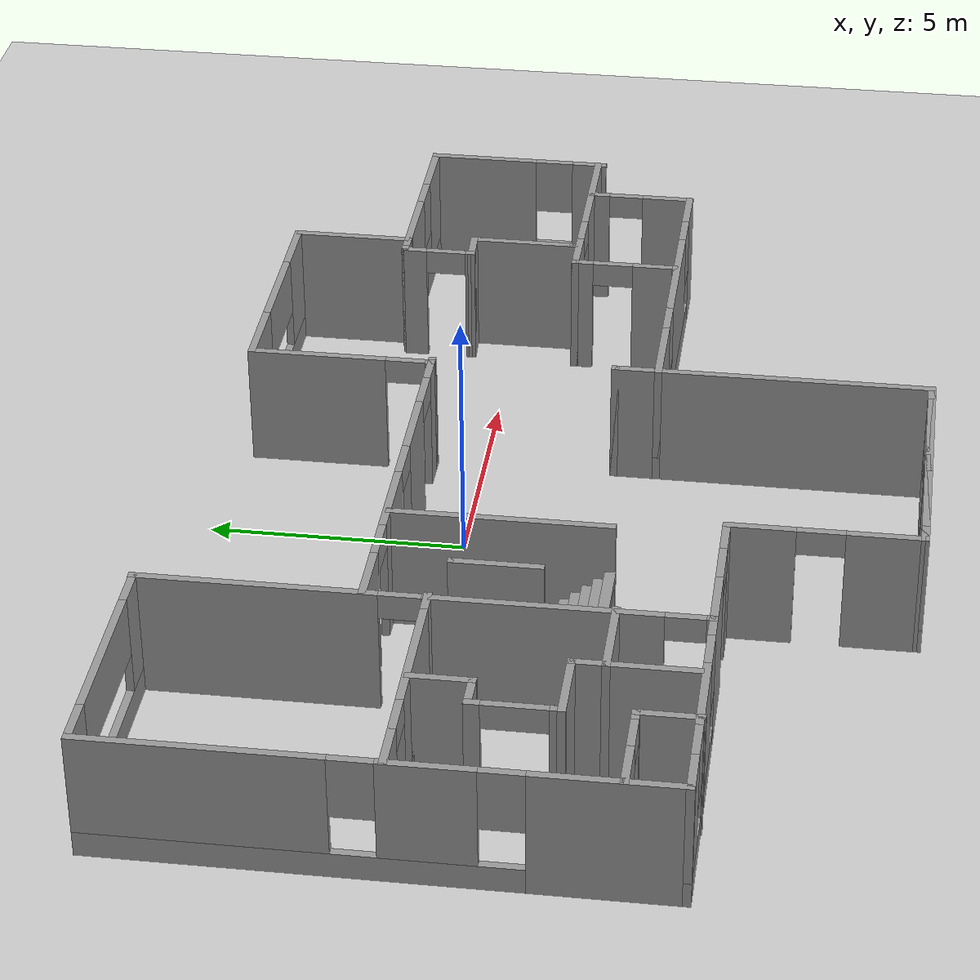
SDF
<sdf version="1.7">
 <world name="default">
  <light name="sun" type="directional">
   <pose>0 0 10 0 -0 0</pose>
   <diffuse>0.8 0.8 0.8 1</diffuse>
   <specular>0.2 0.2 0.2 1</specular>
   <attenuation>
    <range>1000</range>
    <constant>0.9</constant>
    <linear>0.01</linear>
    <quadratic>0.001</quadratic>
   </attenuation>
   <direction>-0.5 0.1 -0.9</direction>
   <spot><inner_angle>0</inner_angle><outer_angle>0</outer_angle><falloff>0</falloff></spot>
  </light>
  <model name="ground_plane">
   <static>1</static>
   <link name="link">
    <collision name="collision">
     <geometry><plane><normal>0 0 1</normal><size>100 100</size></plane></geometry>
     <surface>
      <contact><collide_bitmask>65535</collide_bitmask></contact>
      <friction><ode><mu>100</mu><mu2>50</mu2></ode></friction>
     </surface>
    </collision>
    <visual name="visual">
     <cast_shadows>0</cast_shadows>
     <geometry><plane><normal>0 0 1</normal><size>100 100</size></plane></geometry>
     <material>
      <script><uri>file://media/materials/scripts/gazebo.material</uri><name>Gazebo/Grey</name></script>
     </material>
    </visual>
   </link>
  </model>
  <gravity>0 0 -9.8</gravity>
  <magnetic_field>6e-06 2.3e-05 -4.2e-05</magnetic_field>
  <atmosphere type="adiabatic"/>
  <physics type="ode">
   <max_step_size>0.001</max_step_size>
   <real_time_factor>1</real_time_factor>
   <real_time_update_rate>1000</real_time_update_rate>
  </physics>
  <scene><ambient>0.4 0.4 0.4 1</ambient><background>0.7 0.7 0.7 1</background><shadows>1</shadows></scene>
  <spherical_coordinates>
   <surface_model>EARTH_WGS84</surface_model>
   <latitude_deg>0</latitude_deg>
   <longitude_deg>0</longitude_deg>
   <elevation>0</elevation>
   <heading_deg>0</heading_deg>
  </spherical_coordinates>
  <model name="Floorplan5">
   <pose>0.817084 -1.82012 0 0 -0 0</pose>
   <link name="Stairs_0">
    <visual name="Stairs_0_Visual_0">
     <pose>-5.3338 1.40149 0.083333 0 -0 0</pose>
     <geometry><box><size>1.09051 0.202493 0.166667</size></box></geometry>
     <material>
      <script><uri>file://media/materials/scripts/gazebo.material</uri><name>Gazebo/Grey</name></script>
      <ambient>1 1 1 1</ambient>
     </material>
     <meta><layer>0</layer></meta>
    </visual>
    <collision name="Stairs_0_Collision_0">
     <geometry><box><size>1.09051 0.202493 0.166667</size></box></geometry>
     <pose>-5.3338 1.40149 0.083333 0 -0 0</pose>
    </collision>
    <visual name="Stairs_0_Visual_1">
     <pose>-5.3338 1.199 0.25 0 -0 0</pose>
     <geometry><box><size>1.09051 0.202493 0.166667</size></box></geometry>
     <material>
      <script><uri>file://media/materials/scripts/gazebo.material</uri><name>Gazebo/Grey</name></script>
      <ambient>1 1 1 1</ambient>
     </material>
     <meta><layer>0</layer></meta>
    </visual>
    <collision name="Stairs_0_Collision_1">
     <geometry><box><size>1.09051 0.202493 0.166667</size></box></geometry>
     <pose>-5.3338 1.199 0.25 0 -0 0</pose>
    </collision>
    <visual name="Stairs_0_Visual_2">
     <pose>-5.3338 0.996508 0.416667 0 -0 0</pose>
     <geometry><box><size>1.09051 0.202493 0.166667</size></box></geometry>
     <material>
      <script><uri>file://media/materials/scripts/gazebo.material</uri><name>Gazebo/Grey</name></script>
      <ambient>1 1 1 1</ambient>
     </material>
     <meta><layer>0</layer></meta>
    </visual>
    <collision name="Stairs_0_Collision_2">
     <geometry><box><size>1.09051 0.202493 0.166667</size></box></geometry>
     <pose>-5.3338 0.996508 0.416667 0 -0 0</pose>
    </collision>
    <visual name="Stairs_0_Visual_3">
     <pose>-5.3338 0.794015 0.583333 0 -0 0</pose>
     <geometry><box><size>1.09051 0.202493 0.166667</size></box></geometry>
     <material>
      <script><uri>file://media/materials/scripts/gazebo.material</uri><name>Gazebo/Grey</name></script>
      <ambient>1 1 1 1</ambient>
     </material>
     <meta><layer>0</layer></meta>
    </visual>
    <collision name="Stairs_0_Collision_3">
     <geometry><box><size>1.09051 0.202493 0.166667</size></box></geometry>
     <pose>-5.3338 0.794015 0.583333 0 -0 0</pose>
    </collision>
    <visual name="Stairs_0_Visual_4">
     <pose>-5.3338 0.591523 0.75 0 -0 0</pose>
     <geometry><box><size>1.09051 0.202493 0.166667</size></box></geometry>
     <material>
      <script><uri>file://media/materials/scripts/gazebo.material</uri><name>Gazebo/Grey</name></script>
      <ambient>1 1 1 1</ambient>
     </material>
     <meta><layer>0</layer></meta>
    </visual>
    <collision name="Stairs_0_Collision_4">
     <geometry><box><size>1.09051 0.202493 0.166667</size></box></geometry>
     <pose>-5.3338 0.591523 0.75 0 -0 0</pose>
    </collision>
    <visual name="Stairs_0_Visual_5">
     <pose>-5.3338 0.38903 0.916667 0 -0 0</pose>
     <geometry><box><size>1.09051 0.202493 0.166667</size></box></geometry>
     <material>
      <script><uri>file://media/materials/scripts/gazebo.material</uri><name>Gazebo/Grey</name></script>
      <ambient>1 1 1 1</ambient>
     </material>
     <meta><layer>0</layer></meta>
    </visual>
    <collision name="Stairs_0_Collision_5">
     <geometry><box><size>1.09051 0.202493 0.166667</size></box></geometry>
     <pose>-5.3338 0.38903 0.916667 0 -0 0</pose>
    </collision>
    <visual name="Stairs_0_Visual_6">
     <pose>-5.3338 0.186538 1.08333 0 -0 0</pose>
     <geometry><box><size>1.09051 0.202493 0.166667</size></box></geometry>
     <material>
      <script><uri>file://media/materials/scripts/gazebo.material</uri><name>Gazebo/Grey</name></script>
      <ambient>1 1 1 1</ambient>
     </material>
     <meta><layer>0</layer></meta>
    </visual>
    <collision name="Stairs_0_Collision_6">
     <geometry><box><size>1.09051 0.202493 0.166667</size></box></geometry>
     <pose>-5.3338 0.186538 1.08333 0 -0 0</pose>
    </collision>
    <visual name="Stairs_0_Visual_7">
     <pose>-5.3338 -0.015955 1.25 0 -0 0</pose>
     <geometry><box><size>1.09051 0.202493 0.166667</size></box></geometry>
     <material>
      <script><uri>file://media/materials/scripts/gazebo.material</uri><name>Gazebo/Grey</name></script>
      <ambient>1 1 1 1</ambient>
     </material>
     <meta><layer>0</layer></meta>
    </visual>
    <collision name="Stairs_0_Collision_7">
     <geometry><box><size>1.09051 0.202493 0.166667</size></box></geometry>
     <pose>-5.3338 -0.015955 1.25 0 -0 0</pose>
    </collision>
    <visual name="Stairs_0_Visual_8">
     <pose>-5.3338 -0.218447 1.41667 0 -0 0</pose>
     <geometry><box><size>1.09051 0.202493 0.166667</size></box></geometry>
     <material>
      <script><uri>file://media/materials/scripts/gazebo.material</uri><name>Gazebo/Grey</name></script>
      <ambient>1 1 1 1</ambient>
     </material>
     <meta><layer>0</layer></meta>
    </visual>
    <collision name="Stairs_0_Collision_8">
     <geometry><box><size>1.09051 0.202493 0.166667</size></box></geometry>
     <pose>-5.3338 -0.218447 1.41667 0 -0 0</pose>
    </collision>
    <visual name="Stairs_0_Visual_9">
     <pose>-5.3338 -0.42094 1.58333 0 -0 0</pose>
     <geometry><box><size>1.09051 0.202493 0.166667</size></box></geometry>
     <material>
      <script><uri>file://media/materials/scripts/gazebo.material</uri><name>Gazebo/Grey</name></script>
      <ambient>1 1 1 1</ambient>
     </material>
     <meta><layer>0</layer></meta>
    </visual>
    <collision name="Stairs_0_Collision_9">
     <geometry><box><size>1.09051 0.202493 0.166667</size></box></geometry>
     <pose>-5.3338 -0.42094 1.58333 0 -0 0</pose>
    </collision>
    <visual name="Stairs_0_Visual_10">
     <pose>-5.3338 -0.623432 1.75 0 -0 0</pose>
     <geometry><box><size>1.09051 0.202493 0.166667</size></box></geometry>
     <material>
      <script><uri>file://media/materials/scripts/gazebo.material</uri><name>Gazebo/Grey</name></script>
      <ambient>1 1 1 1</ambient>
     </material>
     <meta><layer>0</layer></meta>
    </visual>
    <collision name="Stairs_0_Collision_10">
     <geometry><box><size>1.09051 0.202493 0.166667</size></box></geometry>
     <pose>-5.3338 -0.623432 1.75 0 -0 0</pose>
    </collision>
    <visual name="Stairs_0_Visual_11">
     <pose>-5.3338 -0.825925 1.91667 0 -0 0</pose>
     <geometry><box><size>1.09051 0.202493 0.166667</size></box></geometry>
     <material>
      <script><uri>file://media/materials/scripts/gazebo.material</uri><name>Gazebo/Grey</name></script>
      <ambient>1 1 1 1</ambient>
     </material>
     <meta><layer>0</layer></meta>
    </visual>
    <collision name="Stairs_0_Collision_11">
     <geometry><box><size>1.09051 0.202493 0.166667</size></box></geometry>
     <pose>-5.3338 -0.825925 1.91667 0 -0 0</pose>
    </collision>
    <visual name="Stairs_0_Visual_12">
     <pose>-5.3338 -1.02842 2.08333 0 -0 0</pose>
     <geometry><box><size>1.09051 0.202493 0.166667</size></box></geometry>
     <material>
      <script><uri>file://media/materials/scripts/gazebo.material</uri><name>Gazebo/Grey</name></script>
      <ambient>1 1 1 1</ambient>
     </material>
     <meta><layer>0</layer></meta>
    </visual>
    <collision name="Stairs_0_Collision_12">
     <geometry><box><size>1.09051 0.202493 0.166667</size></box></geometry>
     <pose>-5.3338 -1.02842 2.08333 0 -0 0</pose>
    </collision>
    <visual name="Stairs_0_Visual_13">
     <pose>-5.3338 -1.23091 2.25 0 -0 0</pose>
     <geometry><box><size>1.09051 0.202493 0.166667</size></box></geometry>
     <material>
      <script><uri>file://media/materials/scripts/gazebo.material</uri><name>Gazebo/Grey</name></script>
      <ambient>1 1 1 1</ambient>
     </material>
     <meta><layer>0</layer></meta>
    </visual>
    <collision name="Stairs_0_Collision_13">
     <geometry><box><size>1.09051 0.202493 0.166667</size></box></geometry>
     <pose>-5.3338 -1.23091 2.25 0 -0 0</pose>
    </collision>
    <visual name="Stairs_0_Visual_14">
     <pose>-5.3338 -1.4334 2.41667 0 -0 0</pose>
     <geometry><box><size>1.09051 0.202493 0.166667</size></box></geometry>
     <material>
      <script><uri>file://media/materials/scripts/gazebo.material</uri><name>Gazebo/Grey</name></script>
      <ambient>1 1 1 1</ambient>
     </material>
     <meta><layer>0</layer></meta>
    </visual>
    <collision name="Stairs_0_Collision_14">
     <geometry><box><size>1.09051 0.202493 0.166667</size></box></geometry>
     <pose>-5.3338 -1.4334 2.41667 0 -0 0</pose>
    </collision>
   </link>
   <link name="Wall_0">
    <collision name="Wall_0_Collision">
     <geometry><box><size>5.33606 0.15 2.5</size></box></geometry>
     <pose>0 0 1.25 0 -0 0</pose>
    </collision>
    <visual name="Wall_0_Visual">
     <pose>0 0 1.25 0 -0 0</pose>
     <geometry><box><size>5.33606 0.15 2.5</size></box></geometry>
     <material>
      <script><uri>file://media/materials/scripts/gazebo.material</uri><name>Gazebo/Grey</name></script>
      <ambient>1 1 1 1</ambient>
     </material>
     <meta><layer>0</layer></meta>
    </visual>
    <pose>-0.430466 -6.98064 0 0 -0 3.13979</pose>
   </link>
   <link name="Wall_1">
    <pose>-3.02349 -5.17596 0 0 -0 1.5708</pose>
    <visual name="Wall_1_Visual_0">
     <pose>-1.12311 0 1.25 0 -0 0</pose>
     <geometry><box><size>1.50379 0.15 2.5</size></box></geometry>
     <material>
      <script><uri>file://media/materials/scripts/gazebo.material</uri><name>Gazebo/Grey</name></script>
      <ambient>1 1 1 1</ambient>
     </material>
     <meta><layer>0</layer></meta>
    </visual>
    <collision name="Wall_1_Collision_0">
     <geometry><box><size>1.50379 0.15 2.5</size></box></geometry>
     <pose>-1.12311 0 1.25 0 -0 0</pose>
    </collision>
    <visual name="Wall_1_Visual_1">
     <pose>1.20189 0 1.25 0 -0 0</pose>
     <geometry><box><size>1.34621 0.15 2.5</size></box></geometry>
     <material>
      <script><uri>file://media/materials/scripts/gazebo.material</uri><name>Gazebo/Grey</name></script>
      <ambient>1 1 1 1</ambient>
     </material>
     <meta><layer>0</layer></meta>
    </visual>
    <collision name="Wall_1_Collision_1">
     <geometry><box><size>1.34621 0.15 2.5</size></box></geometry>
     <pose>1.20189 0 1.25 0 -0 0</pose>
    </collision>
    <visual name="Wall_1_Visual_2">
     <pose>0.078787 0 2.25 0 -0 0</pose>
     <geometry><box><size>0.9 0.15 0.5</size></box></geometry>
     <material>
      <script><uri>file://media/materials/scripts/gazebo.material</uri><name>Gazebo/Grey</name></script>
      <ambient>1 1 1 1</ambient>
     </material>
     <meta><layer>0</layer></meta>
    </visual>
    <collision name="Wall_1_Collision_2">
     <geometry><box><size>0.9 0.15 0.5</size></box></geometry>
     <pose>0.078787 0 2.25 0 -0 0</pose>
    </collision>
   </link>
   <link name="Wall_10">
    <pose>-8.32349 6.97404 0 0 -0 0</pose>
    <visual name="Wall_10_Visual_0">
     <pose>-1.90261 0 1.25 0 -0 0</pose>
     <geometry><box><size>0.944783 0.15 2.5</size></box></geometry>
     <material>
      <script><uri>file://media/materials/scripts/gazebo.material</uri><name>Gazebo/Grey</name></script>
      <ambient>1 1 1 1</ambient>
     </material>
     <meta><layer>0</layer></meta>
    </visual>
    <collision name="Wall_10_Collision_0">
     <geometry><box><size>0.944783 0.15 2.5</size></box></geometry>
     <pose>-1.90261 0 1.25 0 -0 0</pose>
    </collision>
    <visual name="Wall_10_Visual_1">
     <pose>0.472392 0 0.25 0 -0 0</pose>
     <geometry><box><size>3.80522 0.15 0.5</size></box></geometry>
     <material>
      <script><uri>file://media/materials/scripts/gazebo.material</uri><name>Gazebo/Grey</name></script>
      <ambient>1 1 1 1</ambient>
     </material>
     <meta><layer>0</layer></meta>
    </visual>
    <collision name="Wall_10_Collision_1">
     <geometry><box><size>3.80522 0.15 0.5</size></box></geometry>
     <pose>0.472392 0 0.25 0 -0 0</pose>
    </collision>
    <visual name="Wall_10_Visual_2">
     <pose>1.98492 0 1.5 0 -0 0</pose>
     <geometry><box><size>0.78016 0.15 2</size></box></geometry>
     <material>
      <script><uri>file://media/materials/scripts/gazebo.material</uri><name>Gazebo/Grey</name></script>
      <ambient>1 1 1 1</ambient>
     </material>
     <meta><layer>0</layer></meta>
    </visual>
    <collision name="Wall_10_Collision_2">
     <geometry><box><size>0.78016 0.15 2</size></box></geometry>
     <pose>1.98492 0 1.5 0 -0 0</pose>
    </collision>
    <visual name="Wall_10_Visual_3">
     <pose>0.082312 0 1.9 0 -0 0</pose>
     <geometry><box><size>3.02506 0.15 1.2</size></box></geometry>
     <material>
      <script><uri>file://media/materials/scripts/gazebo.material</uri><name>Gazebo/Grey</name></script>
      <ambient>1 1 1 1</ambient>
     </material>
     <meta><layer>0</layer></meta>
    </visual>
    <collision name="Wall_10_Collision_3">
     <geometry><box><size>3.02506 0.15 1.2</size></box></geometry>
     <pose>0.082312 0 1.9 0 -0 0</pose>
    </collision>
   </link>
   <link name="Wall_12">
    <pose>-2.00151 2.83994 0 0 -0 0</pose>
    <visual name="Wall_12_Visual_0">
     <pose>-3.36386 0 1.25 0 -0 0</pose>
     <geometry><box><size>1.27227 0.15 2.5</size></box></geometry>
     <material>
      <script><uri>file://media/materials/scripts/gazebo.material</uri><name>Gazebo/Grey</name></script>
      <ambient>1 1 1 1</ambient>
     </material>
     <meta><layer>0</layer></meta>
    </visual>
    <collision name="Wall_12_Collision_0">
     <geometry><box><size>1.27227 0.15 2.5</size></box></geometry>
     <pose>-3.36386 0 1.25 0 -0 0</pose>
    </collision>
    <visual name="Wall_12_Visual_1">
     <pose>-0.942694 0 1.25 0 -0 0</pose>
     <geometry><box><size>1.77007 0.15 2.5</size></box></geometry>
     <material>
      <script><uri>file://media/materials/scripts/gazebo.material</uri><name>Gazebo/Grey</name></script>
      <ambient>1 1 1 1</ambient>
     </material>
     <meta><layer>0</layer></meta>
    </visual>
    <collision name="Wall_12_Collision_1">
     <geometry><box><size>1.77007 0.15 2.5</size></box></geometry>
     <pose>-0.942694 0 1.25 0 -0 0</pose>
    </collision>
    <visual name="Wall_12_Visual_2">
     <pose>1.63635 0 1.25 0 -0 0</pose>
     <geometry><box><size>1.58802 0.15 2.5</size></box></geometry>
     <material>
      <script><uri>file://media/materials/scripts/gazebo.material</uri><name>Gazebo/Grey</name></script>
      <ambient>1 1 1 1</ambient>
     </material>
     <meta><layer>0</layer></meta>
    </visual>
    <collision name="Wall_12_Collision_2">
     <geometry><box><size>1.58802 0.15 2.5</size></box></geometry>
     <pose>1.63635 0 1.25 0 -0 0</pose>
    </collision>
    <visual name="Wall_12_Visual_3">
     <pose>3.66518 0 1.25 0 -0 0</pose>
     <geometry><box><size>0.669642 0.15 2.5</size></box></geometry>
     <material>
      <script><uri>file://media/materials/scripts/gazebo.material</uri><name>Gazebo/Grey</name></script>
      <ambient>1 1 1 1</ambient>
     </material>
     <meta><layer>0</layer></meta>
    </visual>
    <collision name="Wall_12_Collision_3">
     <geometry><box><size>0.669642 0.15 2.5</size></box></geometry>
     <pose>3.66518 0 1.25 0 -0 0</pose>
    </collision>
    <visual name="Wall_12_Visual_4">
     <pose>-2.27773 0 2.25 0 -0 0</pose>
     <geometry><box><size>0.9 0.15 0.5</size></box></geometry>
     <material>
      <script><uri>file://media/materials/scripts/gazebo.material</uri><name>Gazebo/Grey</name></script>
      <ambient>1 1 1 1</ambient>
     </material>
     <meta><layer>0</layer></meta>
    </visual>
    <collision name="Wall_12_Collision_4">
     <geometry><box><size>0.9 0.15 0.5</size></box></geometry>
     <pose>-2.27773 0 2.25 0 -0 0</pose>
    </collision>
    <visual name="Wall_12_Visual_5">
     <pose>0.39234 0 2.25 0 -0 0</pose>
     <geometry><box><size>0.9 0.15 0.5</size></box></geometry>
     <material>
      <script><uri>file://media/materials/scripts/gazebo.material</uri><name>Gazebo/Grey</name></script>
      <ambient>1 1 1 1</ambient>
     </material>
     <meta><layer>0</layer></meta>
    </visual>
    <collision name="Wall_12_Collision_5">
     <geometry><box><size>0.9 0.15 0.5</size></box></geometry>
     <pose>0.39234 0 2.25 0 -0 0</pose>
    </collision>
    <visual name="Wall_12_Visual_6">
     <pose>2.88036 0 2.25 0 -0 0</pose>
     <geometry><box><size>0.9 0.15 0.5</size></box></geometry>
     <material>
      <script><uri>file://media/materials/scripts/gazebo.material</uri><name>Gazebo/Grey</name></script>
      <ambient>1 1 1 1</ambient>
     </material>
     <meta><layer>0</layer></meta>
    </visual>
    <collision name="Wall_12_Collision_6">
     <geometry><box><size>0.9 0.15 0.5</size></box></geometry>
     <pose>2.88036 0 2.25 0 -0 0</pose>
    </collision>
   </link>
   <link name="Wall_13">
    <collision name="Wall_13_Collision">
     <geometry><box><size>0.25 0.15 2.5</size></box></geometry>
     <pose>0 0 1.25 0 -0 0</pose>
    </collision>
    <visual name="Wall_13_Visual">
     <pose>0 0 1.25 0 -0 0</pose>
     <geometry><box><size>0.25 0.15 2.5</size></box></geometry>
     <material>
      <script><uri>file://media/materials/scripts/gazebo.material</uri><name>Gazebo/Grey</name></script>
      <ambient>1 1 1 1</ambient>
     </material>
     <meta><layer>0</layer></meta>
    </visual>
    <pose>1.97349 2.83994 0 0 -0 0</pose>
   </link>
   <link name="Wall_15">
    <collision name="Wall_15_Collision">
     <geometry><box><size>0.15 0.15 2.5</size></box></geometry>
     <pose>0 0 1.25 0 -0 0</pose>
    </collision>
    <visual name="Wall_15_Visual">
     <pose>0 0 1.25 0 -0 0</pose>
     <geometry><box><size>0.15 0.15 2.5</size></box></geometry>
     <material>
      <script><uri>file://media/materials/scripts/gazebo.material</uri><name>Gazebo/Grey</name></script>
      <ambient>1 1 1 1</ambient>
     </material>
     <meta><layer>0</layer></meta>
    </visual>
    <pose>1.92349 2.83994 0 0 -0 0</pose>
   </link>
   <link name="Wall_17">
    <collision name="Wall_17_Collision">
     <geometry><box><size>0.15 0.15 2.5</size></box></geometry>
     <pose>0 0 1.25 0 -0 0</pose>
    </collision>
    <visual name="Wall_17_Visual">
     <pose>0 0 1.25 0 -0 0</pose>
     <geometry><box><size>0.15 0.15 2.5</size></box></geometry>
     <material>
      <script><uri>file://media/materials/scripts/gazebo.material</uri><name>Gazebo/Grey</name></script>
      <ambient>1 1 1 1</ambient>
     </material>
     <meta><layer>0</layer></meta>
    </visual>
    <pose>1.92349 2.83994 0 0 -0 0</pose>
   </link>
   <link name="Wall_19">
    <pose>1.92349 4.63994 0 0 -0 1.5708</pose>
    <visual name="Wall_19_Visual_0">
     <pose>-1.77755 0 1.25 0 -0 0</pose>
     <geometry><box><size>0.19489 0.15 2.5</size></box></geometry>
     <material>
      <script><uri>file://media/materials/scripts/gazebo.material</uri><name>Gazebo/Grey</name></script>
      <ambient>1 1 1 1</ambient>
     </material>
     <meta><layer>0</layer></meta>
    </visual>
    <collision name="Wall_19_Collision_0">
     <geometry><box><size>0.19489 0.15 2.5</size></box></geometry>
     <pose>-1.77755 0 1.25 0 -0 0</pose>
    </collision>
    <visual name="Wall_19_Visual_1">
     <pose>0.493912 0 1.25 0 -0 0</pose>
     <geometry><box><size>2.76218 0.15 2.5</size></box></geometry>
     <material>
      <script><uri>file://media/materials/scripts/gazebo.material</uri><name>Gazebo/Grey</name></script>
      <ambient>1 1 1 1</ambient>
     </material>
     <meta><layer>0</layer></meta>
    </visual>
    <collision name="Wall_19_Collision_1">
     <geometry><box><size>2.76218 0.15 2.5</size></box></geometry>
     <pose>0.493912 0 1.25 0 -0 0</pose>
    </collision>
    <visual name="Wall_19_Visual_2">
     <pose>-1.28364 0 2.25 0 -0 0</pose>
     <geometry><box><size>0.792934 0.15 0.5</size></box></geometry>
     <material>
      <script><uri>file://media/materials/scripts/gazebo.material</uri><name>Gazebo/Grey</name></script>
      <ambient>1 1 1 1</ambient>
     </material>
     <meta><layer>0</layer></meta>
    </visual>
    <collision name="Wall_19_Collision_2">
     <geometry><box><size>0.792934 0.15 0.5</size></box></geometry>
     <pose>-1.28364 0 2.25 0 -0 0</pose>
    </collision>
   </link>
   <link name="Wall_20">
    <pose>4.34849 6.43994 0 0 -0 0</pose>
    <visual name="Wall_20_Visual_0">
     <pose>-1.71644 0 1.25 0 -0 0</pose>
     <geometry><box><size>1.56712 0.15 2.5</size></box></geometry>
     <material>
      <script><uri>file://media/materials/scripts/gazebo.material</uri><name>Gazebo/Grey</name></script>
      <ambient>1 1 1 1</ambient>
     </material>
     <meta><layer>0</layer></meta>
    </visual>
    <collision name="Wall_20_Collision_0">
     <geometry><box><size>1.56712 0.15 2.5</size></box></geometry>
     <pose>-1.71644 0 1.25 0 -0 0</pose>
    </collision>
    <visual name="Wall_20_Visual_1">
     <pose>0.783562 0 0.25 0 -0 0</pose>
     <geometry><box><size>3.43288 0.15 0.5</size></box></geometry>
     <material>
      <script><uri>file://media/materials/scripts/gazebo.material</uri><name>Gazebo/Grey</name></script>
      <ambient>1 1 1 1</ambient>
     </material>
     <meta><layer>0</layer></meta>
    </visual>
    <collision name="Wall_20_Collision_1">
     <geometry><box><size>3.43288 0.15 0.5</size></box></geometry>
     <pose>0.783562 0 0.25 0 -0 0</pose>
    </collision>
    <visual name="Wall_20_Visual_2">
     <pose>1.82074 0 1.5 0 -0 0</pose>
     <geometry><box><size>1.35853 0.15 2</size></box></geometry>
     <material>
      <script><uri>file://media/materials/scripts/gazebo.material</uri><name>Gazebo/Grey</name></script>
      <ambient>1 1 1 1</ambient>
     </material>
     <meta><layer>0</layer></meta>
    </visual>
    <collision name="Wall_20_Collision_2">
     <geometry><box><size>1.35853 0.15 2</size></box></geometry>
     <pose>1.82074 0 1.5 0 -0 0</pose>
    </collision>
    <visual name="Wall_20_Visual_3">
     <pose>0.104299 0 1.9 0 -0 0</pose>
     <geometry><box><size>2.07435 0.15 1.2</size></box></geometry>
     <material>
      <script><uri>file://media/materials/scripts/gazebo.material</uri><name>Gazebo/Grey</name></script>
      <ambient>1 1 1 1</ambient>
     </material>
     <meta><layer>0</layer></meta>
    </visual>
    <collision name="Wall_20_Collision_3">
     <geometry><box><size>2.07435 0.15 1.2</size></box></geometry>
     <pose>0.104299 0 1.9 0 -0 0</pose>
    </collision>
   </link>
   <link name="Wall_21">
    <collision name="Wall_21_Collision">
     <geometry><box><size>2.5 0.15 2.5</size></box></geometry>
     <pose>0 0 1.25 0 -0 0</pose>
    </collision>
    <visual name="Wall_21_Visual">
     <pose>0 0 1.25 0 -0 0</pose>
     <geometry><box><size>2.5 0.15 2.5</size></box></geometry>
     <material>
      <script><uri>file://media/materials/scripts/gazebo.material</uri><name>Gazebo/Grey</name></script>
      <ambient>1 1 1 1</ambient>
     </material>
     <meta><layer>0</layer></meta>
    </visual>
    <pose>6.77349 5.26494 0 0 -0 -1.5708</pose>
   </link>
   <link name="Wall_22">
    <collision name="Wall_22_Collision">
     <geometry><box><size>0.5 0.15 2.5</size></box></geometry>
     <pose>0 0 1.25 0 -0 0</pose>
    </collision>
    <visual name="Wall_22_Visual">
     <pose>0 0 1.25 0 -0 0</pose>
     <geometry><box><size>0.5 0.15 2.5</size></box></geometry>
     <material>
      <script><uri>file://media/materials/scripts/gazebo.material</uri><name>Gazebo/Grey</name></script>
      <ambient>1 1 1 1</ambient>
     </material>
     <meta><layer>0</layer></meta>
    </visual>
    <pose>6.59849 4.08994 0 0 -0 3.14159</pose>
   </link>
   <link name="Wall_23">
    <collision name="Wall_23_Collision">
     <geometry><box><size>0.15 0.15 2.5</size></box></geometry>
     <pose>0 0 1.25 0 -0 0</pose>
    </collision>
    <visual name="Wall_23_Visual">
     <pose>0 0 1.25 0 -0 0</pose>
     <geometry><box><size>0.15 0.15 2.5</size></box></geometry>
     <material>
      <script><uri>file://media/materials/scripts/gazebo.material</uri><name>Gazebo/Grey</name></script>
      <ambient>1 1 1 1</ambient>
     </material>
     <meta><layer>0</layer></meta>
    </visual>
    <pose>6.42349 4.08994 0 0 -0 0</pose>
   </link>
   <link name="Wall_25">
    <pose>8.69849 4.08994 0 0 -0 0</pose>
    <visual name="Wall_25_Visual_0">
     <pose>-1.12359 0 1.25 0 -0 0</pose>
     <geometry><box><size>1.75281 0.15 2.5</size></box></geometry>
     <material>
      <script><uri>file://media/materials/scripts/gazebo.material</uri><name>Gazebo/Grey</name></script>
      <ambient>1 1 1 1</ambient>
     </material>
     <meta><layer>0</layer></meta>
    </visual>
    <collision name="Wall_25_Collision_0">
     <geometry><box><size>1.75281 0.15 2.5</size></box></geometry>
     <pose>-1.12359 0 1.25 0 -0 0</pose>
    </collision>
    <visual name="Wall_25_Visual_1">
     <pose>0.876405 0 0.25 0 -0 0</pose>
     <geometry><box><size>2.24719 0.15 0.5</size></box></geometry>
     <material>
      <script><uri>file://media/materials/scripts/gazebo.material</uri><name>Gazebo/Grey</name></script>
      <ambient>1 1 1 1</ambient>
     </material>
     <meta><layer>0</layer></meta>
    </visual>
    <collision name="Wall_25_Collision_1">
     <geometry><box><size>2.24719 0.15 0.5</size></box></geometry>
     <pose>0.876405 0 0.25 0 -0 0</pose>
    </collision>
    <visual name="Wall_25_Visual_2">
     <pose>1.27641 0 1.5 0 -0 0</pose>
     <geometry><box><size>1.44719 0.15 2</size></box></geometry>
     <material>
      <script><uri>file://media/materials/scripts/gazebo.material</uri><name>Gazebo/Grey</name></script>
      <ambient>1 1 1 1</ambient>
     </material>
     <meta><layer>0</layer></meta>
    </visual>
    <collision name="Wall_25_Collision_2">
     <geometry><box><size>1.44719 0.15 2</size></box></geometry>
     <pose>1.27641 0 1.5 0 -0 0</pose>
    </collision>
    <visual name="Wall_25_Visual_3">
     <pose>0.15281 0 1.9 0 -0 0</pose>
     <geometry><box><size>0.8 0.15 1.2</size></box></geometry>
     <material>
      <script><uri>file://media/materials/scripts/gazebo.material</uri><name>Gazebo/Grey</name></script>
      <ambient>1 1 1 1</ambient>
     </material>
     <meta><layer>0</layer></meta>
    </visual>
    <collision name="Wall_25_Collision_3">
     <geometry><box><size>0.8 0.15 1.2</size></box></geometry>
     <pose>0.15281 0 1.9 0 -0 0</pose>
    </collision>
   </link>
   <link name="Wall_26">
    <pose>10.6235 2.28994 0 0 -0 -1.5708</pose>
    <visual name="Wall_26_Visual_0">
     <pose>-0.720844 0 1.25 0 -0 0</pose>
     <geometry><box><size>2.30831 0.15 2.5</size></box></geometry>
     <material>
      <script><uri>file://media/materials/scripts/gazebo.material</uri><name>Gazebo/Grey</name></script>
      <ambient>1 1 1 1</ambient>
     </material>
     <meta><layer>0</layer></meta>
    </visual>
    <collision name="Wall_26_Collision_0">
     <geometry><box><size>2.30831 0.15 2.5</size></box></geometry>
     <pose>-0.720844 0 1.25 0 -0 0</pose>
    </collision>
    <visual name="Wall_26_Visual_1">
     <pose>1.15416 0 0.25 0 -0 0</pose>
     <geometry><box><size>1.44169 0.15 0.5</size></box></geometry>
     <material>
      <script><uri>file://media/materials/scripts/gazebo.material</uri><name>Gazebo/Grey</name></script>
      <ambient>1 1 1 1</ambient>
     </material>
     <meta><layer>0</layer></meta>
    </visual>
    <collision name="Wall_26_Collision_1">
     <geometry><box><size>1.44169 0.15 0.5</size></box></geometry>
     <pose>1.15416 0 0.25 0 -0 0</pose>
    </collision>
    <visual name="Wall_26_Visual_2">
     <pose>1.55416 0 1.5 0 -0 0</pose>
     <geometry><box><size>0.641688 0.15 2</size></box></geometry>
     <material>
      <script><uri>file://media/materials/scripts/gazebo.material</uri><name>Gazebo/Grey</name></script>
      <ambient>1 1 1 1</ambient>
     </material>
     <meta><layer>0</layer></meta>
    </visual>
    <collision name="Wall_26_Collision_2">
     <geometry><box><size>0.641688 0.15 2</size></box></geometry>
     <pose>1.55416 0 1.5 0 -0 0</pose>
    </collision>
    <visual name="Wall_26_Visual_3">
     <pose>0.833312 0 1.9 0 -0 0</pose>
     <geometry><box><size>0.8 0.15 1.2</size></box></geometry>
     <material>
      <script><uri>file://media/materials/scripts/gazebo.material</uri><name>Gazebo/Grey</name></script>
      <ambient>1 1 1 1</ambient>
     </material>
     <meta><layer>0</layer></meta>
    </visual>
    <collision name="Wall_26_Collision_3">
     <geometry><box><size>0.8 0.15 1.2</size></box></geometry>
     <pose>0.833312 0 1.9 0 -0 0</pose>
    </collision>
   </link>
   <link name="Wall_27">
    <collision name="Wall_27_Collision">
     <geometry><box><size>0.25 0.15 2.5</size></box></geometry>
     <pose>0 0 1.25 0 -0 0</pose>
    </collision>
    <visual name="Wall_27_Visual">
     <pose>0 0 1.25 0 -0 0</pose>
     <geometry><box><size>0.25 0.15 2.5</size></box></geometry>
     <material>
      <script><uri>file://media/materials/scripts/gazebo.material</uri><name>Gazebo/Grey</name></script>
      <ambient>1 1 1 1</ambient>
     </material>
     <meta><layer>0</layer></meta>
    </visual>
    <pose>10.6235 0.439942 0 0 -0 -1.5708</pose>
   </link>
   <link name="Wall_29">
    <pose>8.44849 0.489942 0 0 -0 3.14159</pose>
    <visual name="Wall_29_Visual_0">
     <pose>-0.899015 0 1.25 0 -0 0</pose>
     <geometry><box><size>2.70197 0.15 2.5</size></box></geometry>
     <material>
      <script><uri>file://media/materials/scripts/gazebo.material</uri><name>Gazebo/Grey</name></script>
      <ambient>1 1 1 1</ambient>
     </material>
     <meta><layer>0</layer></meta>
    </visual>
    <collision name="Wall_29_Collision_0">
     <geometry><box><size>2.70197 0.15 2.5</size></box></geometry>
     <pose>-0.899015 0 1.25 0 -0 0</pose>
    </collision>
    <visual name="Wall_29_Visual_1">
     <pose>1.71686 0 1.25 0 -0 0</pose>
     <geometry><box><size>1.06628 0.15 2.5</size></box></geometry>
     <material>
      <script><uri>file://media/materials/scripts/gazebo.material</uri><name>Gazebo/Grey</name></script>
      <ambient>1 1 1 1</ambient>
     </material>
     <meta><layer>0</layer></meta>
    </visual>
    <collision name="Wall_29_Collision_1">
     <geometry><box><size>1.06628 0.15 2.5</size></box></geometry>
     <pose>1.71686 0 1.25 0 -0 0</pose>
    </collision>
    <visual name="Wall_29_Visual_2">
     <pose>0.817847 0 2.25 0 -0 0</pose>
     <geometry><box><size>0.731754 0.15 0.5</size></box></geometry>
     <material>
      <script><uri>file://media/materials/scripts/gazebo.material</uri><name>Gazebo/Grey</name></script>
      <ambient>1 1 1 1</ambient>
     </material>
     <meta><layer>0</layer></meta>
    </visual>
    <collision name="Wall_29_Collision_2">
     <geometry><box><size>0.731754 0.15 0.5</size></box></geometry>
     <pose>0.817847 0 2.25 0 -0 0</pose>
    </collision>
   </link>
   <link name="Wall_30">
    <collision name="Wall_30_Collision">
     <geometry><box><size>0.15 0.15 2.5</size></box></geometry>
     <pose>0 0 1.25 0 -0 0</pose>
    </collision>
    <visual name="Wall_30_Visual">
     <pose>0 0 1.25 0 -0 0</pose>
     <geometry><box><size>0.15 0.15 2.5</size></box></geometry>
     <material>
      <script><uri>file://media/materials/scripts/gazebo.material</uri><name>Gazebo/Grey</name></script>
      <ambient>1 1 1 1</ambient>
     </material>
     <meta><layer>0</layer></meta>
    </visual>
    <pose>6.27349 0.489942 0 0 -0 0</pose>
   </link>
   <link name="Wall_32">
    <pose>6.36151 3.36099 0 0 -0 -1.5708</pose>
    <visual name="Wall_32_Visual_0">
     <pose>-0.510408 0 1.25 0 -0 0</pose>
     <geometry><box><size>0.479183 0.15 2.5</size></box></geometry>
     <material>
      <script><uri>file://media/materials/scripts/gazebo.material</uri><name>Gazebo/Grey</name></script>
      <ambient>1 1 1 1</ambient>
     </material>
     <meta><layer>0</layer></meta>
    </visual>
    <collision name="Wall_32_Collision_0">
     <geometry><box><size>0.479183 0.15 2.5</size></box></geometry>
     <pose>-0.510408 0 1.25 0 -0 0</pose>
    </collision>
    <visual name="Wall_32_Visual_1">
     <pose>0.650239 0 1.25 0 -0 0</pose>
     <geometry><box><size>0.199522 0.15 2.5</size></box></geometry>
     <material>
      <script><uri>file://media/materials/scripts/gazebo.material</uri><name>Gazebo/Grey</name></script>
      <ambient>1 1 1 1</ambient>
     </material>
     <meta><layer>0</layer></meta>
    </visual>
    <collision name="Wall_32_Collision_1">
     <geometry><box><size>0.199522 0.15 2.5</size></box></geometry>
     <pose>0.650239 0 1.25 0 -0 0</pose>
    </collision>
    <visual name="Wall_32_Visual_2">
     <pose>0.139831 0 2.25 0 -0 0</pose>
     <geometry><box><size>0.821295 0.15 0.5</size></box></geometry>
     <material>
      <script><uri>file://media/materials/scripts/gazebo.material</uri><name>Gazebo/Grey</name></script>
      <ambient>1 1 1 1</ambient>
     </material>
     <meta><layer>0</layer></meta>
    </visual>
    <collision name="Wall_32_Collision_2">
     <geometry><box><size>0.821295 0.15 0.5</size></box></geometry>
     <pose>0.139831 0 2.25 0 -0 0</pose>
    </collision>
   </link>
   <link name="Wall_33">
    <collision name="Wall_33_Collision">
     <geometry><box><size>0.75 0.15 2.5</size></box></geometry>
     <pose>0 0 1.25 0 -0 0</pose>
    </collision>
    <visual name="Wall_33_Visual">
     <pose>0 0 1.25 0 -0 0</pose>
     <geometry><box><size>0.75 0.15 2.5</size></box></geometry>
     <material>
      <script><uri>file://media/materials/scripts/gazebo.material</uri><name>Gazebo/Grey</name></script>
      <ambient>1 1 1 1</ambient>
     </material>
     <meta><layer>0</layer></meta>
    </visual>
    <pose>6.66151 2.69929 0 0 -0 0.044305</pose>
   </link>
   <link name="Wall_34">
    <collision name="Wall_34_Collision">
     <geometry><box><size>2.25 0.15 2.5</size></box></geometry>
     <pose>0 0 1.25 0 -0 0</pose>
    </collision>
    <visual name="Wall_34_Visual">
     <pose>0 0 1.25 0 -0 0</pose>
     <geometry><box><size>2.25 0.15 2.5</size></box></geometry>
     <material>
      <script><uri>file://media/materials/scripts/gazebo.material</uri><name>Gazebo/Grey</name></script>
      <ambient>1 1 1 1</ambient>
     </material>
     <meta><layer>0</layer></meta>
    </visual>
    <pose>6.96151 1.64929 0 0 -0 -1.5708</pose>
   </link>
   <link name="Wall_35">
    <collision name="Wall_35_Collision">
     <geometry><box><size>0.15 0.15 2.5</size></box></geometry>
     <pose>0 0 1.25 0 -0 0</pose>
    </collision>
    <visual name="Wall_35_Visual">
     <pose>0 0 1.25 0 -0 0</pose>
     <geometry><box><size>0.15 0.15 2.5</size></box></geometry>
     <material>
      <script><uri>file://media/materials/scripts/gazebo.material</uri><name>Gazebo/Grey</name></script>
      <ambient>1 1 1 1</ambient>
     </material>
     <meta><layer>0</layer></meta>
    </visual>
    <pose>6.96151 0.612589 0 0 -0 0</pose>
   </link>
   <link name="Wall_37">
    <pose>9.26256 -0.585315 0 0 -0 -1.5708</pose>
    <visual name="Wall_37_Visual_0">
     <pose>-0.899951 0 1.25 0 -0 0</pose>
     <geometry><box><size>0.450099 0.15 2.5</size></box></geometry>
     <material>
      <script><uri>file://media/materials/scripts/gazebo.material</uri><name>Gazebo/Grey</name></script>
      <ambient>1 1 1 1</ambient>
     </material>
     <meta><layer>0</layer></meta>
    </visual>
    <collision name="Wall_37_Collision_0">
     <geometry><box><size>0.450099 0.15 2.5</size></box></geometry>
     <pose>-0.899951 0 1.25 0 -0 0</pose>
    </collision>
    <visual name="Wall_37_Visual_1">
     <pose>0.583279 0 1.25 0 -0 0</pose>
     <geometry><box><size>1.08344 0.15 2.5</size></box></geometry>
     <material>
      <script><uri>file://media/materials/scripts/gazebo.material</uri><name>Gazebo/Grey</name></script>
      <ambient>1 1 1 1</ambient>
     </material>
     <meta><layer>0</layer></meta>
    </visual>
    <collision name="Wall_37_Collision_1">
     <geometry><box><size>1.08344 0.15 2.5</size></box></geometry>
     <pose>0.583279 0 1.25 0 -0 0</pose>
    </collision>
    <visual name="Wall_37_Visual_2">
     <pose>-0.316672 0 2.25 0 -0 0</pose>
     <geometry><box><size>0.716459 0.15 0.5</size></box></geometry>
     <material>
      <script><uri>file://media/materials/scripts/gazebo.material</uri><name>Gazebo/Grey</name></script>
      <ambient>1 1 1 1</ambient>
     </material>
     <meta><layer>0</layer></meta>
    </visual>
    <collision name="Wall_37_Collision_2">
     <geometry><box><size>0.716459 0.15 0.5</size></box></geometry>
     <pose>-0.316672 0 2.25 0 -0 0</pose>
    </collision>
   </link>
   <link name="Wall_38">
    <pose>5.71256 -1.63532 0 0 -0 3.14159</pose>
    <visual name="Wall_38_Visual_0">
     <pose>-3.0964 0 1.25 0 -0 0</pose>
     <geometry><box><size>1.05719 0.15 2.5</size></box></geometry>
     <material>
      <script><uri>file://media/materials/scripts/gazebo.material</uri><name>Gazebo/Grey</name></script>
      <ambient>1 1 1 1</ambient>
     </material>
     <meta><layer>0</layer></meta>
    </visual>
    <collision name="Wall_38_Collision_0">
     <geometry><box><size>1.05719 0.15 2.5</size></box></geometry>
     <pose>-3.0964 0 1.25 0 -0 0</pose>
    </collision>
    <visual name="Wall_38_Visual_1">
     <pose>0.528596 0 0.25 0 -0 0</pose>
     <geometry><box><size>6.19281 0.15 0.5</size></box></geometry>
     <material>
      <script><uri>file://media/materials/scripts/gazebo.material</uri><name>Gazebo/Grey</name></script>
      <ambient>1 1 1 1</ambient>
     </material>
     <meta><layer>0</layer></meta>
    </visual>
    <collision name="Wall_38_Collision_1">
     <geometry><box><size>6.19281 0.15 0.5</size></box></geometry>
     <pose>0.528596 0 0.25 0 -0 0</pose>
    </collision>
    <visual name="Wall_38_Visual_2">
     <pose>-0.337194 0 1.5 0 -0 0</pose>
     <geometry><box><size>2.86123 0.15 2</size></box></geometry>
     <material>
      <script><uri>file://media/materials/scripts/gazebo.material</uri><name>Gazebo/Grey</name></script>
      <ambient>1 1 1 1</ambient>
     </material>
     <meta><layer>0</layer></meta>
    </visual>
    <collision name="Wall_38_Collision_2">
     <geometry><box><size>2.86123 0.15 2</size></box></geometry>
     <pose>-0.337194 0 1.5 0 -0 0</pose>
    </collision>
    <visual name="Wall_38_Visual_3">
     <pose>2.75921 0 1.5 0 -0 0</pose>
     <geometry><box><size>1.73158 0.15 2</size></box></geometry>
     <material>
      <script><uri>file://media/materials/scripts/gazebo.material</uri><name>Gazebo/Grey</name></script>
      <ambient>1 1 1 1</ambient>
     </material>
     <meta><layer>0</layer></meta>
    </visual>
    <collision name="Wall_38_Collision_3">
     <geometry><box><size>1.73158 0.15 2</size></box></geometry>
     <pose>2.75921 0 1.5 0 -0 0</pose>
    </collision>
    <visual name="Wall_38_Visual_4">
     <pose>-2.16781 0 1.9 0 -0 0</pose>
     <geometry><box><size>0.8 0.15 1.2</size></box></geometry>
     <material>
      <script><uri>file://media/materials/scripts/gazebo.material</uri><name>Gazebo/Grey</name></script>
      <ambient>1 1 1 1</ambient>
     </material>
     <meta><layer>0</layer></meta>
    </visual>
    <collision name="Wall_38_Collision_4">
     <geometry><box><size>0.8 0.15 1.2</size></box></geometry>
     <pose>-2.16781 0 1.9 0 -0 0</pose>
    </collision>
    <visual name="Wall_38_Visual_5">
     <pose>1.49342 0 1.9 0 -0 0</pose>
     <geometry><box><size>0.8 0.15 1.2</size></box></geometry>
     <material>
      <script><uri>file://media/materials/scripts/gazebo.material</uri><name>Gazebo/Grey</name></script>
      <ambient>1 1 1 1</ambient>
     </material>
     <meta><layer>0</layer></meta>
    </visual>
    <collision name="Wall_38_Collision_5">
     <geometry><box><size>0.8 0.15 1.2</size></box></geometry>
     <pose>1.49342 0 1.9 0 -0 0</pose>
    </collision>
   </link>
   <link name="Wall_39">
    <collision name="Wall_39_Collision">
     <geometry><box><size>1 0.15 2.5</size></box></geometry>
     <pose>0 0 1.25 0 -0 0</pose>
    </collision>
    <visual name="Wall_39_Visual">
     <pose>0 0 1.25 0 -0 0</pose>
     <geometry><box><size>1 0.15 2.5</size></box></geometry>
     <material>
      <script><uri>file://media/materials/scripts/gazebo.material</uri><name>Gazebo/Grey</name></script>
      <ambient>1 1 1 1</ambient>
     </material>
     <meta><layer>0</layer></meta>
    </visual>
    <pose>2.16256 -1.21032 0 0 -0 1.5708</pose>
   </link>
   <link name="Wall_40">
    <collision name="Wall_40_Collision">
     <geometry><box><size>0.15 0.15 2.5</size></box></geometry>
     <pose>0 0 1.25 0 -0 0</pose>
    </collision>
    <visual name="Wall_40_Visual">
     <pose>0 0 1.25 0 -0 0</pose>
     <geometry><box><size>0.15 0.15 2.5</size></box></geometry>
     <material>
      <script><uri>file://media/materials/scripts/gazebo.material</uri><name>Gazebo/Grey</name></script>
      <ambient>1 1 1 1</ambient>
     </material>
     <meta><layer>0</layer></meta>
    </visual>
    <pose>2.16256 -0.785315 0 0 -0 0</pose>
   </link>
   <link name="Wall_42">
    <collision name="Wall_42_Collision">
     <geometry><box><size>5.5 0.15 2.5</size></box></geometry>
     <pose>0 0 1.25 0 -0 0</pose>
    </collision>
    <visual name="Wall_42_Visual">
     <pose>0 0 1.25 0 -0 0</pose>
     <geometry><box><size>5.5 0.15 2.5</size></box></geometry>
     <material>
      <script><uri>file://media/materials/scripts/gazebo.material</uri><name>Gazebo/Grey</name></script>
      <ambient>1 1 1 1</ambient>
     </material>
     <meta><layer>0</layer></meta>
    </visual>
    <pose>2.16256 -4.31032 0 0 -0 -1.5708</pose>
   </link>
   <link name="Wall_43">
    <pose>-0.430466 -6.98064 0 0 -0 3.13979</pose>
    <visual name="Wall_43_Visual_0">
     <pose>-2.44294 0 1.25 0 -0 0</pose>
     <geometry><box><size>0.450176 0.15 2.5</size></box></geometry>
     <material>
      <script><uri>file://media/materials/scripts/gazebo.material</uri><name>Gazebo/Grey</name></script>
      <ambient>1 1 1 1</ambient>
     </material>
     <meta><layer>0</layer></meta>
    </visual>
    <collision name="Wall_43_Collision_0">
     <geometry><box><size>0.450176 0.15 2.5</size></box></geometry>
     <pose>-2.44294 0 1.25 0 -0 0</pose>
    </collision>
    <visual name="Wall_43_Visual_1">
     <pose>0.225088 0 0.25 0 -0 0</pose>
     <geometry><box><size>4.88588 0.15 0.5</size></box></geometry>
     <material>
      <script><uri>file://media/materials/scripts/gazebo.material</uri><name>Gazebo/Grey</name></script>
      <ambient>1 1 1 1</ambient>
     </material>
     <meta><layer>0</layer></meta>
    </visual>
    <collision name="Wall_43_Collision_1">
     <geometry><box><size>4.88588 0.15 0.5</size></box></geometry>
     <pose>0.225088 0 0.25 0 -0 0</pose>
    </collision>
    <visual name="Wall_43_Visual_2">
     <pose>0.053397 0 1.5 0 -0 0</pose>
     <geometry><box><size>0.555406 0.15 2</size></box></geometry>
     <material>
      <script><uri>file://media/materials/scripts/gazebo.material</uri><name>Gazebo/Grey</name></script>
      <ambient>1 1 1 1</ambient>
     </material>
     <meta><layer>0</layer></meta>
    </visual>
    <collision name="Wall_43_Collision_2">
     <geometry><box><size>0.555406 0.15 2</size></box></geometry>
     <pose>0.053397 0 1.5 0 -0 0</pose>
    </collision>
    <visual name="Wall_43_Visual_3">
     <pose>2.42547 0 1.5 0 -0 0</pose>
     <geometry><box><size>0.485123 0.15 2</size></box></geometry>
     <material>
      <script><uri>file://media/materials/scripts/gazebo.material</uri><name>Gazebo/Grey</name></script>
      <ambient>1 1 1 1</ambient>
     </material>
     <meta><layer>0</layer></meta>
    </visual>
    <collision name="Wall_43_Collision_3">
     <geometry><box><size>0.485123 0.15 2</size></box></geometry>
     <pose>2.42547 0 1.5 0 -0 0</pose>
    </collision>
    <visual name="Wall_43_Visual_4">
     <pose>-1.22108 0 1.9 0 -0 0</pose>
     <geometry><box><size>1.99355 0.15 1.2</size></box></geometry>
     <material>
      <script><uri>file://media/materials/scripts/gazebo.material</uri><name>Gazebo/Grey</name></script>
      <ambient>1 1 1 1</ambient>
     </material>
     <meta><layer>0</layer></meta>
    </visual>
    <collision name="Wall_43_Collision_4">
     <geometry><box><size>1.99355 0.15 1.2</size></box></geometry>
     <pose>-1.22108 0 1.9 0 -0 0</pose>
    </collision>
    <visual name="Wall_43_Visual_5">
     <pose>1.257 0 1.9 0 -0 0</pose>
     <geometry><box><size>1.85181 0.15 1.2</size></box></geometry>
     <material>
      <script><uri>file://media/materials/scripts/gazebo.material</uri><name>Gazebo/Grey</name></script>
      <ambient>1 1 1 1</ambient>
     </material>
     <meta><layer>0</layer></meta>
    </visual>
    <collision name="Wall_43_Collision_5">
     <geometry><box><size>1.85181 0.15 1.2</size></box></geometry>
     <pose>1.257 0 1.9 0 -0 0</pose>
    </collision>
   </link>
   <link name="Wall_44">
    <collision name="Wall_44_Collision">
     <geometry><box><size>0.16 0.15 2.5</size></box></geometry>
     <pose>0 0 1.25 0 -0 0</pose>
    </collision>
    <visual name="Wall_44_Visual">
     <pose>0 0 1.25 0 -0 0</pose>
     <geometry><box><size>0.16 0.15 2.5</size></box></geometry>
     <material>
      <script><uri>file://media/materials/scripts/gazebo.material</uri><name>Gazebo/Grey</name></script>
      <ambient>1 1 1 1</ambient>
     </material>
     <meta><layer>0</layer></meta>
    </visual>
    <pose>-3.01849 -6.97596 0 0 -0 0</pose>
   </link>
   <link name="Wall_46">
    <pose>6.27349 -0.560058 0 0 -0 -1.5708</pose>
    <visual name="Wall_46_Visual_0">
     <pose>-0.898794 0 1.25 0 -0 0</pose>
     <geometry><box><size>0.452413 0.15 2.5</size></box></geometry>
     <material>
      <script><uri>file://media/materials/scripts/gazebo.material</uri><name>Gazebo/Grey</name></script>
      <ambient>1 1 1 1</ambient>
     </material>
     <meta><layer>0</layer></meta>
    </visual>
    <collision name="Wall_46_Collision_0">
     <geometry><box><size>0.452413 0.15 2.5</size></box></geometry>
     <pose>-0.898794 0 1.25 0 -0 0</pose>
    </collision>
    <visual name="Wall_46_Visual_1">
     <pose>0.637969 0 1.25 0 -0 0</pose>
     <geometry><box><size>0.974063 0.15 2.5</size></box></geometry>
     <material>
      <script><uri>file://media/materials/scripts/gazebo.material</uri><name>Gazebo/Grey</name></script>
      <ambient>1 1 1 1</ambient>
     </material>
     <meta><layer>0</layer></meta>
    </visual>
    <collision name="Wall_46_Collision_1">
     <geometry><box><size>0.974063 0.15 2.5</size></box></geometry>
     <pose>0.637969 0 1.25 0 -0 0</pose>
    </collision>
    <visual name="Wall_46_Visual_2">
     <pose>-0.260825 0 2.25 0 -0 0</pose>
     <geometry><box><size>0.823524 0.15 0.5</size></box></geometry>
     <material>
      <script><uri>file://media/materials/scripts/gazebo.material</uri><name>Gazebo/Grey</name></script>
      <ambient>1 1 1 1</ambient>
     </material>
     <meta><layer>0</layer></meta>
    </visual>
    <collision name="Wall_46_Collision_2">
     <geometry><box><size>0.823524 0.15 0.5</size></box></geometry>
     <pose>-0.260825 0 2.25 0 -0 0</pose>
    </collision>
   </link>
   <link name="Wall_47">
    <collision name="Wall_47_Collision">
     <geometry><box><size>0.15 0.15 2.5</size></box></geometry>
     <pose>0 0 1.25 0 -0 0</pose>
    </collision>
    <visual name="Wall_47_Visual">
     <pose>0 0 1.25 0 -0 0</pose>
     <geometry><box><size>0.15 0.15 2.5</size></box></geometry>
     <material>
      <script><uri>file://media/materials/scripts/gazebo.material</uri><name>Gazebo/Grey</name></script>
      <ambient>1 1 1 1</ambient>
     </material>
     <meta><layer>0</layer></meta>
    </visual>
    <pose>6.27349 -1.61006 0 0 -0 0</pose>
   </link>
   <link name="Wall_49">
    <collision name="Wall_49_Collision">
     <geometry><box><size>4.25 0.15 2.5</size></box></geometry>
     <pose>0 0 1.25 0 -0 0</pose>
    </collision>
    <visual name="Wall_49_Visual">
     <pose>0 0 1.25 0 -0 0</pose>
     <geometry><box><size>4.25 0.15 2.5</size></box></geometry>
     <material>
      <script><uri>file://media/materials/scripts/gazebo.material</uri><name>Gazebo/Grey</name></script>
      <ambient>1 1 1 1</ambient>
     </material>
     <meta><layer>0</layer></meta>
    </visual>
    <pose>-3.34876 0.736864 0 0 -0 1.5708</pose>
   </link>
   <link name="Wall_5">
    <pose>-5.95393 1.81045 0 0 -0 -1.5708</pose>
    <visual name="Wall_5_Visual_0">
     <pose>-2.99965 0 1.25 0 -0 0</pose>
     <geometry><box><size>4.50069 0.15 2.5</size></box></geometry>
     <material>
      <script><uri>file://media/materials/scripts/gazebo.material</uri><name>Gazebo/Grey</name></script>
      <ambient>1 1 1 1</ambient>
     </material>
     <meta><layer>0</layer></meta>
    </visual>
    <collision name="Wall_5_Collision_0">
     <geometry><box><size>4.50069 0.15 2.5</size></box></geometry>
     <pose>-2.99965 0 1.25 0 -0 0</pose>
    </collision>
    <visual name="Wall_5_Visual_1">
     <pose>2.1786 0 1.25 0 -0 0</pose>
     <geometry><box><size>4.29854 0.15 2.5</size></box></geometry>
     <material>
      <script><uri>file://media/materials/scripts/gazebo.material</uri><name>Gazebo/Grey</name></script>
      <ambient>1 1 1 1</ambient>
     </material>
     <meta><layer>0</layer></meta>
    </visual>
    <collision name="Wall_5_Collision_1">
     <geometry><box><size>4.29854 0.15 2.5</size></box></geometry>
     <pose>2.1786 0 1.25 0 -0 0</pose>
    </collision>
    <visual name="Wall_5_Visual_2">
     <pose>5.15802 0 1.25 0 -0 0</pose>
     <geometry><box><size>0.183955 0.15 2.5</size></box></geometry>
     <material>
      <script><uri>file://media/materials/scripts/gazebo.material</uri><name>Gazebo/Grey</name></script>
      <ambient>1 1 1 1</ambient>
     </material>
     <meta><layer>0</layer></meta>
    </visual>
    <collision name="Wall_5_Collision_2">
     <geometry><box><size>0.183955 0.15 2.5</size></box></geometry>
     <pose>5.15802 0 1.25 0 -0 0</pose>
    </collision>
    <visual name="Wall_5_Visual_3">
     <pose>-0.359991 0 2.25 0 -0 0</pose>
     <geometry><box><size>0.778633 0.15 0.5</size></box></geometry>
     <material>
      <script><uri>file://media/materials/scripts/gazebo.material</uri><name>Gazebo/Grey</name></script>
      <ambient>1 1 1 1</ambient>
     </material>
     <meta><layer>0</layer></meta>
    </visual>
    <collision name="Wall_5_Collision_3">
     <geometry><box><size>0.778633 0.15 0.5</size></box></geometry>
     <pose>-0.359991 0 2.25 0 -0 0</pose>
    </collision>
    <visual name="Wall_5_Visual_4">
     <pose>4.69696 0 2.25 0 -0 0</pose>
     <geometry><box><size>0.738178 0.15 0.5</size></box></geometry>
     <material>
      <script><uri>file://media/materials/scripts/gazebo.material</uri><name>Gazebo/Grey</name></script>
      <ambient>1 1 1 1</ambient>
     </material>
     <meta><layer>0</layer></meta>
    </visual>
    <collision name="Wall_5_Collision_4">
     <geometry><box><size>0.738178 0.15 0.5</size></box></geometry>
     <pose>4.69696 0 2.25 0 -0 0</pose>
    </collision>
   </link>
   <link name="Wall_50">
    <collision name="Wall_50_Collision">
     <geometry><box><size>0.15 0.15 2.5</size></box></geometry>
     <pose>0 0 1.25 0 -0 0</pose>
    </collision>
    <visual name="Wall_50_Visual">
     <pose>0 0 1.25 0 -0 0</pose>
     <geometry><box><size>0.15 0.15 2.5</size></box></geometry>
     <material>
      <script><uri>file://media/materials/scripts/gazebo.material</uri><name>Gazebo/Grey</name></script>
      <ambient>1 1 1 1</ambient>
     </material>
     <meta><layer>0</layer></meta>
    </visual>
    <pose>-3.34876 2.78686 0 0 -0 0</pose>
   </link>
   <link name="Wall_52">
    <pose>-8.41531 1.68058 0 0 -0 0</pose>
    <visual name="Wall_52_Visual_0">
     <pose>-1.78515 0 1.25 0 -0 0</pose>
     <geometry><box><size>0.929692 0.15 2.5</size></box></geometry>
     <material>
      <script><uri>file://media/materials/scripts/gazebo.material</uri><name>Gazebo/Grey</name></script>
      <ambient>1 1 1 1</ambient>
     </material>
     <meta><layer>0</layer></meta>
    </visual>
    <collision name="Wall_52_Collision_0">
     <geometry><box><size>0.929692 0.15 2.5</size></box></geometry>
     <pose>-1.78515 0 1.25 0 -0 0</pose>
    </collision>
    <visual name="Wall_52_Visual_1">
     <pose>0.864277 0 1.25 0 -0 0</pose>
     <geometry><box><size>2.77145 0.15 2.5</size></box></geometry>
     <material>
      <script><uri>file://media/materials/scripts/gazebo.material</uri><name>Gazebo/Grey</name></script>
      <ambient>1 1 1 1</ambient>
     </material>
     <meta><layer>0</layer></meta>
    </visual>
    <collision name="Wall_52_Collision_1">
     <geometry><box><size>2.77145 0.15 2.5</size></box></geometry>
     <pose>0.864277 0 1.25 0 -0 0</pose>
    </collision>
    <visual name="Wall_52_Visual_2">
     <pose>-0.920877 0 2.25 0 -0 0</pose>
     <geometry><box><size>0.798861 0.15 0.5</size></box></geometry>
     <material>
      <script><uri>file://media/materials/scripts/gazebo.material</uri><name>Gazebo/Grey</name></script>
      <ambient>1 1 1 1</ambient>
     </material>
     <meta><layer>0</layer></meta>
    </visual>
    <collision name="Wall_52_Collision_2">
     <geometry><box><size>0.798861 0.15 0.5</size></box></geometry>
     <pose>-0.920877 0 2.25 0 -0 0</pose>
    </collision>
   </link>
   <link name="Wall_53">
    <collision name="Wall_53_Collision">
     <geometry><box><size>0.5 0.15 2.5</size></box></geometry>
     <pose>0 0 1.25 0 -0 0</pose>
    </collision>
    <visual name="Wall_53_Visual">
     <pose>0 0 1.25 0 -0 0</pose>
     <geometry><box><size>0.5 0.15 2.5</size></box></geometry>
     <material>
      <script><uri>file://media/materials/scripts/gazebo.material</uri><name>Gazebo/Grey</name></script>
      <ambient>1 1 1 1</ambient>
     </material>
     <meta><layer>0</layer></meta>
    </visual>
    <pose>-6.06531 1.68058 0 0 -0 0</pose>
   </link>
   <link name="Wall_54">
    <collision name="Wall_54_Collision">
     <geometry><box><size>0.15 0.15 2.5</size></box></geometry>
     <pose>0 0 1.25 0 -0 0</pose>
    </collision>
    <visual name="Wall_54_Visual">
     <pose>0 0 1.25 0 -0 0</pose>
     <geometry><box><size>0.15 0.15 2.5</size></box></geometry>
     <material>
      <script><uri>file://media/materials/scripts/gazebo.material</uri><name>Gazebo/Grey</name></script>
      <ambient>1 1 1 1</ambient>
     </material>
     <meta><layer>0</layer></meta>
    </visual>
    <pose>-5.89031 1.68058 0 0 -0 0</pose>
   </link>
   <link name="Wall_56">
    <collision name="Wall_56_Collision">
     <geometry><box><size>1.75 0.15 2.5</size></box></geometry>
     <pose>0 0 1.25 0 -0 0</pose>
    </collision>
    <visual name="Wall_56_Visual">
     <pose>0 0 1.25 0 -0 0</pose>
     <geometry><box><size>1.75 0.15 2.5</size></box></geometry>
     <material>
      <script><uri>file://media/materials/scripts/gazebo.material</uri><name>Gazebo/Grey</name></script>
      <ambient>1 1 1 1</ambient>
     </material>
     <meta><layer>0</layer></meta>
    </visual>
    <pose>-6.69746 -1.65701 0 0 -0 3.14159</pose>
   </link>
   <link name="Wall_57">
    <collision name="Wall_57_Collision">
     <geometry><box><size>1.75 0.15 2.5</size></box></geometry>
     <pose>0 0 1.25 0 -0 0</pose>
    </collision>
    <visual name="Wall_57_Visual">
     <pose>0 0 1.25 0 -0 0</pose>
     <geometry><box><size>1.75 0.15 2.5</size></box></geometry>
     <material>
      <script><uri>file://media/materials/scripts/gazebo.material</uri><name>Gazebo/Grey</name></script>
      <ambient>1 1 1 1</ambient>
     </material>
     <meta><layer>0</layer></meta>
    </visual>
    <pose>-7.49746 -2.45701 0 0 -0 -1.5708</pose>
   </link>
   <link name="Wall_59">
    <collision name="Wall_59_Collision">
     <geometry><box><size>0.75 0.15 2.5</size></box></geometry>
     <pose>0 0 1.25 0 -0 0</pose>
    </collision>
    <visual name="Wall_59_Visual">
     <pose>0 0 1.25 0 -0 0</pose>
     <geometry><box><size>0.75 0.15 2.5</size></box></geometry>
     <material>
      <script><uri>file://media/materials/scripts/gazebo.material</uri><name>Gazebo/Grey</name></script>
      <ambient>1 1 1 1</ambient>
     </material>
     <meta><layer>0</layer></meta>
    </visual>
    <pose>-7.49746 -1.35701 0 0 -0 1.5708</pose>
   </link>
   <link name="Wall_6">
    <collision name="Wall_6_Collision">
     <geometry><box><size>0.15 0.15 2.5</size></box></geometry>
     <pose>0 0 1.25 0 -0 0</pose>
    </collision>
    <visual name="Wall_6_Visual">
     <pose>0 0 1.25 0 -0 0</pose>
     <geometry><box><size>0.15 0.15 2.5</size></box></geometry>
     <material>
      <script><uri>file://media/materials/scripts/gazebo.material</uri><name>Gazebo/Grey</name></script>
      <ambient>1 1 1 1</ambient>
     </material>
     <meta><layer>0</layer></meta>
    </visual>
    <pose>-5.95393 -3.37335 0 0 -0 0</pose>
   </link>
   <link name="Wall_60">
    <collision name="Wall_60_Collision">
     <geometry><box><size>1.5 0.15 2.5</size></box></geometry>
     <pose>0 0 1.25 0 -0 0</pose>
    </collision>
    <visual name="Wall_60_Visual">
     <pose>0 0 1.25 0 -0 0</pose>
     <geometry><box><size>1.5 0.15 2.5</size></box></geometry>
     <material>
      <script><uri>file://media/materials/scripts/gazebo.material</uri><name>Gazebo/Grey</name></script>
      <ambient>1 1 1 1</ambient>
     </material>
     <meta><layer>0</layer></meta>
    </visual>
    <pose>-8.17246 -1.05701 0 0 -0 3.14159</pose>
   </link>
   <link name="Wall_61">
    <pose>-8.84746 -0.257008 0 0 -0 1.5708</pose>
    <visual name="Wall_61_Visual_0">
     <pose>-0.735439 0 1.25 0 -0 0</pose>
     <geometry><box><size>0.279123 0.15 2.5</size></box></geometry>
     <material>
      <script><uri>file://media/materials/scripts/gazebo.material</uri><name>Gazebo/Grey</name></script>
      <ambient>1 1 1 1</ambient>
     </material>
     <meta><layer>0</layer></meta>
    </visual>
    <collision name="Wall_61_Collision_0">
     <geometry><box><size>0.279123 0.15 2.5</size></box></geometry>
     <pose>-0.735439 0 1.25 0 -0 0</pose>
    </collision>
    <visual name="Wall_61_Visual_1">
     <pose>0.731156 0 1.25 0 -0 0</pose>
     <geometry><box><size>0.287688 0.15 2.5</size></box></geometry>
     <material>
      <script><uri>file://media/materials/scripts/gazebo.material</uri><name>Gazebo/Grey</name></script>
      <ambient>1 1 1 1</ambient>
     </material>
     <meta><layer>0</layer></meta>
    </visual>
    <collision name="Wall_61_Collision_1">
     <geometry><box><size>0.287688 0.15 2.5</size></box></geometry>
     <pose>0.731156 0 1.25 0 -0 0</pose>
    </collision>
    <visual name="Wall_61_Visual_2">
     <pose>-0.004283 0 2.25 0 -0 0</pose>
     <geometry><box><size>1.18319 0.15 0.5</size></box></geometry>
     <material>
      <script><uri>file://media/materials/scripts/gazebo.material</uri><name>Gazebo/Grey</name></script>
      <ambient>1 1 1 1</ambient>
     </material>
     <meta><layer>0</layer></meta>
    </visual>
    <collision name="Wall_61_Collision_2">
     <geometry><box><size>1.18319 0.15 0.5</size></box></geometry>
     <pose>-0.004283 0 2.25 0 -0 0</pose>
    </collision>
   </link>
   <link name="Wall_62">
    <collision name="Wall_62_Collision">
     <geometry><box><size>0.75 0.15 2.5</size></box></geometry>
     <pose>0 0 1.25 0 -0 0</pose>
    </collision>
    <visual name="Wall_62_Visual">
     <pose>0 0 1.25 0 -0 0</pose>
     <geometry><box><size>0.75 0.15 2.5</size></box></geometry>
     <material>
      <script><uri>file://media/materials/scripts/gazebo.material</uri><name>Gazebo/Grey</name></script>
      <ambient>1 1 1 1</ambient>
     </material>
     <meta><layer>0</layer></meta>
    </visual>
    <pose>-8.54746 0.542992 0 0 -0 0</pose>
   </link>
   <link name="Wall_63">
    <collision name="Wall_63_Collision">
     <geometry><box><size>1.25 0.15 2.5</size></box></geometry>
     <pose>0 0 1.25 0 -0 0</pose>
    </collision>
    <visual name="Wall_63_Visual">
     <pose>0 0 1.25 0 -0 0</pose>
     <geometry><box><size>1.25 0.15 2.5</size></box></geometry>
     <material>
      <script><uri>file://media/materials/scripts/gazebo.material</uri><name>Gazebo/Grey</name></script>
      <ambient>1 1 1 1</ambient>
     </material>
     <meta><layer>0</layer></meta>
    </visual>
    <pose>-8.24746 1.09299 0 0 -0 1.5708</pose>
   </link>
   <link name="Wall_64">
    <collision name="Wall_64_Collision">
     <geometry><box><size>0.15 0.15 2.5</size></box></geometry>
     <pose>0 0 1.25 0 -0 0</pose>
    </collision>
    <visual name="Wall_64_Visual">
     <pose>0 0 1.25 0 -0 0</pose>
     <geometry><box><size>0.15 0.15 2.5</size></box></geometry>
     <material>
      <script><uri>file://media/materials/scripts/gazebo.material</uri><name>Gazebo/Grey</name></script>
      <ambient>1 1 1 1</ambient>
     </material>
     <meta><layer>0</layer></meta>
    </visual>
    <pose>-8.24746 1.64299 0 0 -0 0</pose>
   </link>
   <link name="Wall_66">
    <collision name="Wall_66_Collision">
     <geometry><box><size>1.25 0.15 2.5</size></box></geometry>
     <pose>0 0 1.25 0 -0 0</pose>
    </collision>
    <visual name="Wall_66_Visual">
     <pose>0 0 1.25 0 -0 0</pose>
     <geometry><box><size>1.25 0.15 2.5</size></box></geometry>
     <material>
      <script><uri>file://media/materials/scripts/gazebo.material</uri><name>Gazebo/Grey</name></script>
      <ambient>1 1 1 1</ambient>
     </material>
     <meta><layer>0</layer></meta>
    </visual>
    <pose>-8.7698 -2.8466 0 0 -0 1.5708</pose>
   </link>
   <link name="Wall_67">
    <pose>-9.69481 -2.2966 0 0 -0 3.14159</pose>
    <visual name="Wall_67_Visual_0">
     <pose>-0.863855 0 1.25 0 -0 0</pose>
     <geometry><box><size>0.27229 0.15 2.5</size></box></geometry>
     <material>
      <script><uri>file://media/materials/scripts/gazebo.material</uri><name>Gazebo/Grey</name></script>
      <ambient>1 1 1 1</ambient>
     </material>
     <meta><layer>0</layer></meta>
    </visual>
    <collision name="Wall_67_Collision_0">
     <geometry><box><size>0.27229 0.15 2.5</size></box></geometry>
     <pose>-0.863855 0 1.25 0 -0 0</pose>
    </collision>
    <visual name="Wall_67_Visual_1">
     <pose>0.49512 0 1.25 0 -0 0</pose>
     <geometry><box><size>1.00976 0.15 2.5</size></box></geometry>
     <material>
      <script><uri>file://media/materials/scripts/gazebo.material</uri><name>Gazebo/Grey</name></script>
      <ambient>1 1 1 1</ambient>
     </material>
     <meta><layer>0</layer></meta>
    </visual>
    <collision name="Wall_67_Collision_1">
     <geometry><box><size>1.00976 0.15 2.5</size></box></geometry>
     <pose>0.49512 0 1.25 0 -0 0</pose>
    </collision>
    <visual name="Wall_67_Visual_2">
     <pose>-0.368735 0 2.25 0 -0 0</pose>
     <geometry><box><size>0.71795 0.15 0.5</size></box></geometry>
     <material>
      <script><uri>file://media/materials/scripts/gazebo.material</uri><name>Gazebo/Grey</name></script>
      <ambient>1 1 1 1</ambient>
     </material>
     <meta><layer>0</layer></meta>
    </visual>
    <collision name="Wall_67_Collision_2">
     <geometry><box><size>0.71795 0.15 0.5</size></box></geometry>
     <pose>-0.368735 0 2.25 0 -0 0</pose>
    </collision>
   </link>
   <link name="Wall_68">
    <collision name="Wall_68_Collision">
     <geometry><box><size>0.16 0.15 2.5</size></box></geometry>
     <pose>0 0 1.25 0 -0 0</pose>
    </collision>
    <visual name="Wall_68_Visual">
     <pose>0 0 1.25 0 -0 0</pose>
     <geometry><box><size>0.16 0.15 2.5</size></box></geometry>
     <material>
      <script><uri>file://media/materials/scripts/gazebo.material</uri><name>Gazebo/Grey</name></script>
      <ambient>1 1 1 1</ambient>
     </material>
     <meta><layer>0</layer></meta>
    </visual>
    <pose>-10.6148 -2.2966 0 0 -0 0</pose>
   </link>
   <link name="Wall_70">
    <collision name="Wall_70_Collision">
     <geometry><box><size>1.75 0.15 2.5</size></box></geometry>
     <pose>0 0 1.25 0 -0 0</pose>
    </collision>
    <visual name="Wall_70_Visual">
     <pose>0 0 1.25 0 -0 0</pose>
     <geometry><box><size>1.75 0.15 2.5</size></box></geometry>
     <material>
      <script><uri>file://media/materials/scripts/gazebo.material</uri><name>Gazebo/Grey</name></script>
      <ambient>1 1 1 1</ambient>
     </material>
     <meta><layer>0</layer></meta>
    </visual>
    <pose>-4.78493 0.61962 0 0 -0 1.5708</pose>
   </link>
   <link name="Wall_71">
    <collision name="Wall_71_Collision">
     <geometry><box><size>0.15 0.15 2.5</size></box></geometry>
     <pose>0 0 1.25 0 -0 0</pose>
    </collision>
    <visual name="Wall_71_Visual">
     <pose>0 0 1.25 0 -0 0</pose>
     <geometry><box><size>0.15 0.15 2.5</size></box></geometry>
     <material>
      <script><uri>file://media/materials/scripts/gazebo.material</uri><name>Gazebo/Grey</name></script>
      <ambient>1 1 1 1</ambient>
     </material>
     <meta><layer>0</layer></meta>
    </visual>
    <pose>-4.78493 1.41962 0 0 -0 0</pose>
   </link>
   <link name="Wall_8">
    <pose>-6.82349 -3.37596 0 0 -0 3.14159</pose>
    <visual name="Wall_8_Visual_0">
     <pose>-3.45485 0 1.25 0 -0 0</pose>
     <geometry><box><size>0.84029 0.15 2.5</size></box></geometry>
     <material>
      <script><uri>file://media/materials/scripts/gazebo.material</uri><name>Gazebo/Grey</name></script>
      <ambient>1 1 1 1</ambient>
     </material>
     <meta><layer>0</layer></meta>
    </visual>
    <collision name="Wall_8_Collision_0">
     <geometry><box><size>0.84029 0.15 2.5</size></box></geometry>
     <pose>-3.45485 0 1.25 0 -0 0</pose>
    </collision>
    <visual name="Wall_8_Visual_1">
     <pose>-1.25637 0 1.25 0 -0 0</pose>
     <geometry><box><size>1.75668 0.15 2.5</size></box></geometry>
     <material>
      <script><uri>file://media/materials/scripts/gazebo.material</uri><name>Gazebo/Grey</name></script>
      <ambient>1 1 1 1</ambient>
     </material>
     <meta><layer>0</layer></meta>
    </visual>
    <collision name="Wall_8_Collision_1">
     <geometry><box><size>1.75668 0.15 2.5</size></box></geometry>
     <pose>-1.25637 0 1.25 0 -0 0</pose>
    </collision>
    <visual name="Wall_8_Visual_2">
     <pose>1.74849 0 0.25 0 -0 0</pose>
     <geometry><box><size>4.25303 0.15 0.5</size></box></geometry>
     <material>
      <script><uri>file://media/materials/scripts/gazebo.material</uri><name>Gazebo/Grey</name></script>
      <ambient>1 1 1 1</ambient>
     </material>
     <meta><layer>0</layer></meta>
    </visual>
    <collision name="Wall_8_Collision_2">
     <geometry><box><size>4.25303 0.15 0.5</size></box></geometry>
     <pose>1.74849 0 0.25 0 -0 0</pose>
    </collision>
    <visual name="Wall_8_Visual_3">
     <pose>1.28621 0 1.5 0 -0 0</pose>
     <geometry><box><size>1.72847 0.15 2</size></box></geometry>
     <material>
      <script><uri>file://media/materials/scripts/gazebo.material</uri><name>Gazebo/Grey</name></script>
      <ambient>1 1 1 1</ambient>
     </material>
     <meta><layer>0</layer></meta>
    </visual>
    <collision name="Wall_8_Collision_3">
     <geometry><box><size>1.72847 0.15 2</size></box></geometry>
     <pose>1.28621 0 1.5 0 -0 0</pose>
    </collision>
    <visual name="Wall_8_Visual_4">
     <pose>3.41272 0 1.5 0 -0 0</pose>
     <geometry><box><size>0.924556 0.15 2</size></box></geometry>
     <material>
      <script><uri>file://media/materials/scripts/gazebo.material</uri><name>Gazebo/Grey</name></script>
      <ambient>1 1 1 1</ambient>
     </material>
     <meta><layer>0</layer></meta>
    </visual>
    <collision name="Wall_8_Collision_4">
     <geometry><box><size>0.924556 0.15 2</size></box></geometry>
     <pose>3.41272 0 1.5 0 -0 0</pose>
    </collision>
    <visual name="Wall_8_Visual_5">
     <pose>0.021971 0 1.9 0 -0 0</pose>
     <geometry><box><size>0.8 0.15 1.2</size></box></geometry>
     <material>
      <script><uri>file://media/materials/scripts/gazebo.material</uri><name>Gazebo/Grey</name></script>
      <ambient>1 1 1 1</ambient>
     </material>
     <meta><layer>0</layer></meta>
    </visual>
    <collision name="Wall_8_Collision_5">
     <geometry><box><size>0.8 0.15 1.2</size></box></geometry>
     <pose>0.021971 0 1.9 0 -0 0</pose>
    </collision>
    <visual name="Wall_8_Visual_6">
     <pose>2.55044 0 1.9 0 -0 0</pose>
     <geometry><box><size>0.8 0.15 1.2</size></box></geometry>
     <material>
      <script><uri>file://media/materials/scripts/gazebo.material</uri><name>Gazebo/Grey</name></script>
      <ambient>1 1 1 1</ambient>
     </material>
     <meta><layer>0</layer></meta>
    </visual>
    <collision name="Wall_8_Collision_6">
     <geometry><box><size>0.8 0.15 1.2</size></box></geometry>
     <pose>2.55044 0 1.9 0 -0 0</pose>
    </collision>
    <visual name="Wall_8_Visual_7">
     <pose>-2.58471 0 2.25 0 -0 0</pose>
     <geometry><box><size>0.9 0.15 0.5</size></box></geometry>
     <material>
      <script><uri>file://media/materials/scripts/gazebo.material</uri><name>Gazebo/Grey</name></script>
      <ambient>1 1 1 1</ambient>
     </material>
     <meta><layer>0</layer></meta>
    </visual>
    <collision name="Wall_8_Collision_7">
     <geometry><box><size>0.9 0.15 0.5</size></box></geometry>
     <pose>-2.58471 0 2.25 0 -0 0</pose>
    </collision>
   </link>
   <link name="Wall_9">
    <pose>-10.6235 1.79904 0 0 -0 1.5708</pose>
    <visual name="Wall_9_Visual_0">
     <pose>-3.866 0 1.25 0 -0 0</pose>
     <geometry><box><size>2.768 0.15 2.5</size></box></geometry>
     <material>
      <script><uri>file://media/materials/scripts/gazebo.material</uri><name>Gazebo/Grey</name></script>
      <ambient>1 1 1 1</ambient>
     </material>
     <meta><layer>0</layer></meta>
    </visual>
    <collision name="Wall_9_Collision_0">
     <geometry><box><size>2.768 0.15 2.5</size></box></geometry>
     <pose>-3.866 0 1.25 0 -0 0</pose>
    </collision>
    <visual name="Wall_9_Visual_1">
     <pose>1.384 0 0.25 0 -0 0</pose>
     <geometry><box><size>7.732 0.15 0.5</size></box></geometry>
     <material>
      <script><uri>file://media/materials/scripts/gazebo.material</uri><name>Gazebo/Grey</name></script>
      <ambient>1 1 1 1</ambient>
     </material>
     <meta><layer>0</layer></meta>
    </visual>
    <collision name="Wall_9_Collision_1">
     <geometry><box><size>7.732 0.15 0.5</size></box></geometry>
     <pose>1.384 0 0.25 0 -0 0</pose>
    </collision>
    <visual name="Wall_9_Visual_2">
     <pose>-0.827877 0 1.5 0 -0 0</pose>
     <geometry><box><size>1.70825 0.15 2</size></box></geometry>
     <material>
      <script><uri>file://media/materials/scripts/gazebo.material</uri><name>Gazebo/Grey</name></script>
      <ambient>1 1 1 1</ambient>
     </material>
     <meta><layer>0</layer></meta>
    </visual>
    <collision name="Wall_9_Collision_2">
     <geometry><box><size>1.70825 0.15 2</size></box></geometry>
     <pose>-0.827877 0 1.5 0 -0 0</pose>
    </collision>
    <visual name="Wall_9_Visual_3">
     <pose>3.03812 0 1.5 0 -0 0</pose>
     <geometry><box><size>4.42375 0.15 2</size></box></geometry>
     <material>
      <script><uri>file://media/materials/scripts/gazebo.material</uri><name>Gazebo/Grey</name></script>
      <ambient>1 1 1 1</ambient>
     </material>
     <meta><layer>0</layer></meta>
    </visual>
    <collision name="Wall_9_Collision_3">
     <geometry><box><size>4.42375 0.15 2</size></box></geometry>
     <pose>3.03812 0 1.5 0 -0 0</pose>
    </collision>
    <visual name="Wall_9_Visual_4">
     <pose>-2.082 0 1.9 0 -0 0</pose>
     <geometry><box><size>0.8 0.15 1.2</size></box></geometry>
     <material>
      <script><uri>file://media/materials/scripts/gazebo.material</uri><name>Gazebo/Grey</name></script>
      <ambient>1 1 1 1</ambient>
     </material>
     <meta><layer>0</layer></meta>
    </visual>
    <collision name="Wall_9_Collision_4">
     <geometry><box><size>0.8 0.15 1.2</size></box></geometry>
     <pose>-2.082 0 1.9 0 -0 0</pose>
    </collision>
    <visual name="Wall_9_Visual_5">
     <pose>0.426246 0 1.9 0 -0 0</pose>
     <geometry><box><size>0.8 0.15 1.2</size></box></geometry>
     <material>
      <script><uri>file://media/materials/scripts/gazebo.material</uri><name>Gazebo/Grey</name></script>
      <ambient>1 1 1 1</ambient>
     </material>
     <meta><layer>0</layer></meta>
    </visual>
    <collision name="Wall_9_Collision_5">
     <geometry><box><size>0.8 0.15 1.2</size></box></geometry>
     <pose>0.426246 0 1.9 0 -0 0</pose>
    </collision>
   </link>
   <static>1</static>
  </model>
 </world>
</sdf>
